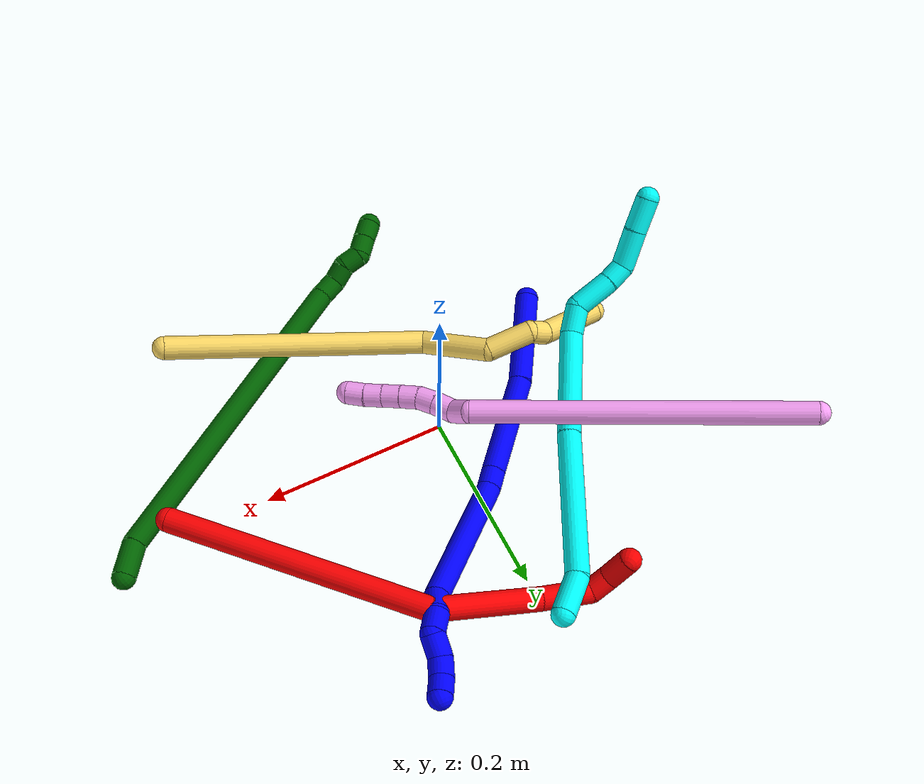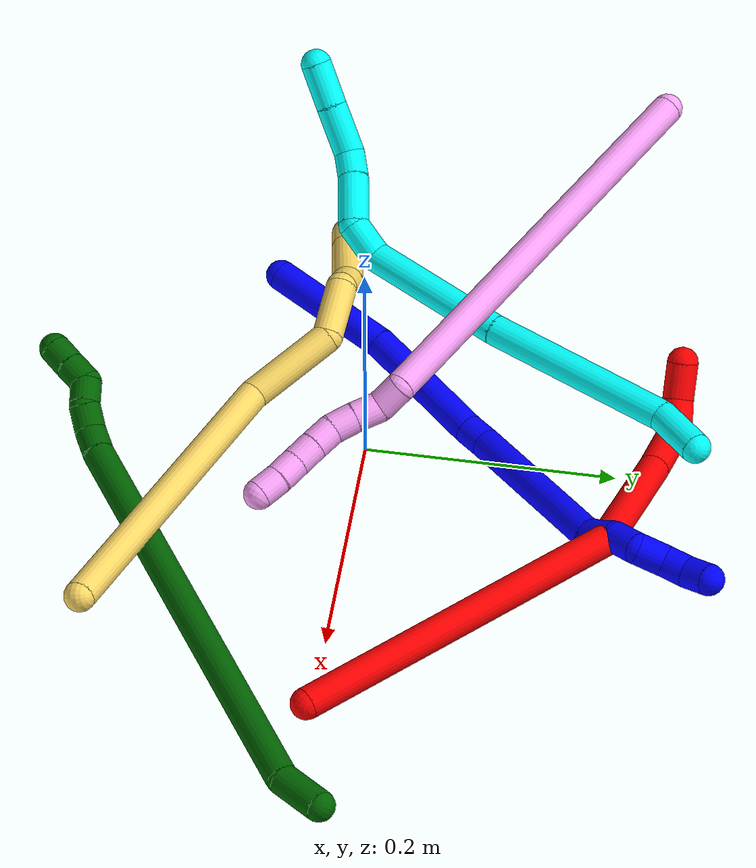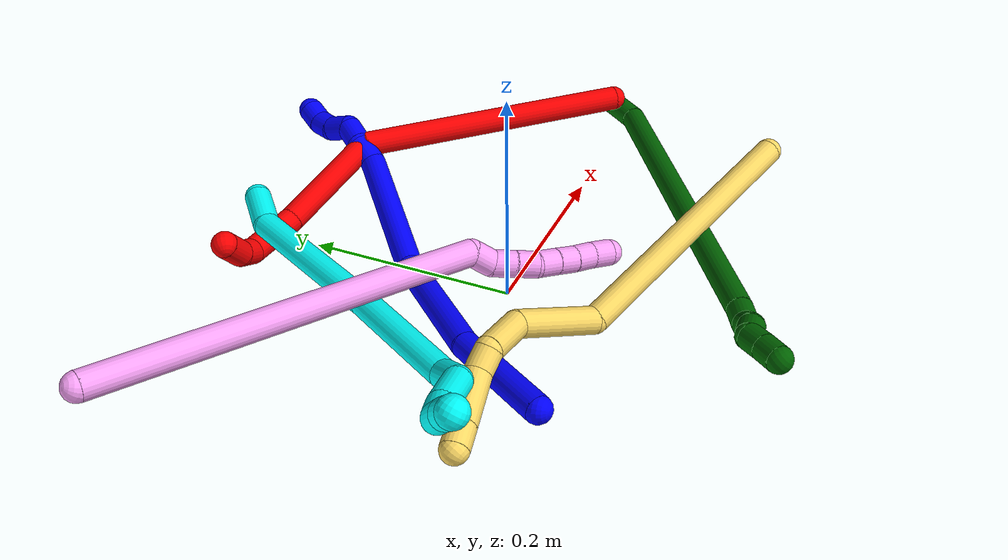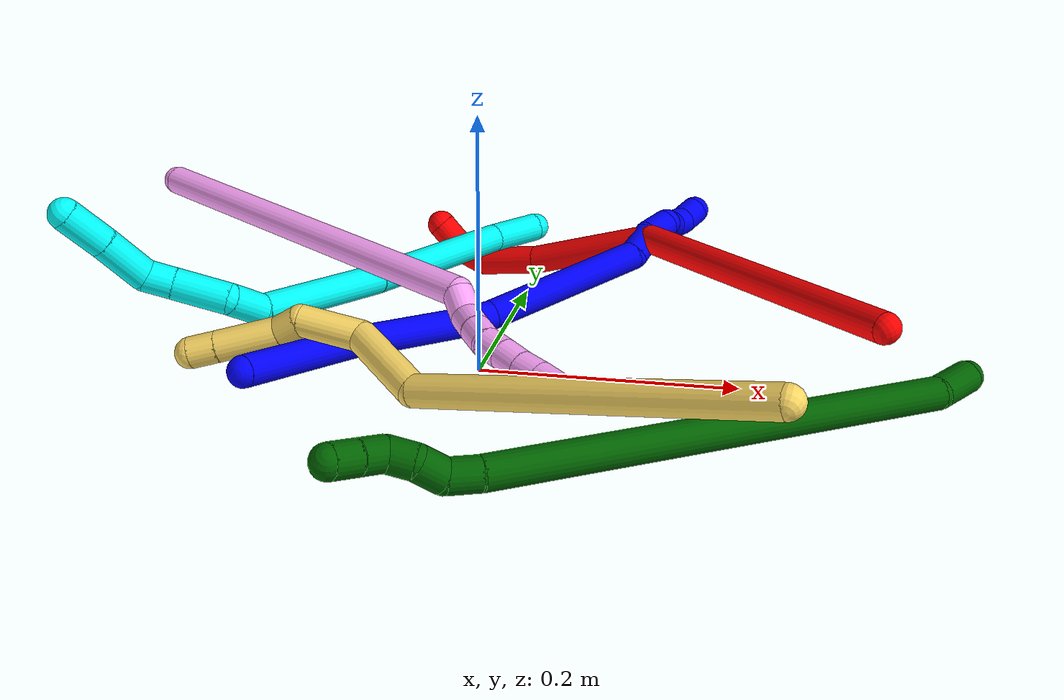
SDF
<sdf version="1.7">
 <world name="default">
  <plugin name="TubeGeneratorPlugin" filename="libtube_generator_plugin.so"/>
  <model name="photoneo_s_sensor">
   <static>1</static>
   <pose>0 0 2 1.57079 1.57079 3.14159</pose>
   <link name="link">
    <inertial><mass>0.1</mass></inertial>
    <sensor name="sensor" type="depth">
     <update_rate>30</update_rate>
     <camera>
      <horizontal_fov>1.22</horizontal_fov>
      <image><width>1920</width><height>1200</height><format>B8G8R8</format></image>
      <clip><near>0.1</near><far>4</far></clip>
      <depth_camera><output>points</output></depth_camera>
     </camera>
     <plugin name="camera_plugin" filename="libgazebo_ros_depth_camera.so">
      <baseline>0.2</baseline>
      <alwaysOn>1</alwaysOn>
      <updateRate>0.0</updateRate>
      <cameraName>camera_ir</cameraName>
      <imageTopicName>/camera/color/image_raw</imageTopicName>
      <cameraInfoTopicName>/camera/color/camera_info</cameraInfoTopicName>
      <depthImageTopicName>/camera/depth/image_raw</depthImageTopicName>
      <depthImageCameraInfoTopicName>/camera/depth/camera_info</depthImageCameraInfoTopicName>
      <pointCloudTopicName>/camera/depth/points</pointCloudTopicName>
      <frameName>fr_optical</frameName>
      <pointCloudCutoff>0.1</pointCloudCutoff>
      <pointCloudCutoffMax>2.0</pointCloudCutoffMax>
      <distortionK1>0</distortionK1>
      <distortionK2>0</distortionK2>
      <distortionK3>0</distortionK3>
      <distortionT1>0</distortionT1>
      <distortionT2>0</distortionT2>
      <CxPrime>0</CxPrime>
      <Cx>0</Cx>
      <Cy>0</Cy>
      <focalLength>0</focalLength>
      <hackBaseline>0</hackBaseline>
     </plugin>
    </sensor>
   </link>
  </model>
  <gravity>0 0 -9.8</gravity>
  <magnetic_field>6e-06 2.3e-05 -4.2e-05</magnetic_field>
  <atmosphere type="adiabatic"/>
  <physics name="default_physics" default="0" type="ode">
   <max_step_size>0.003</max_step_size>
   <real_time_factor>1</real_time_factor>
   <real_time_update_rate>1000</real_time_update_rate>
   <max_contacts>10000</max_contacts>
   <ode>
    <solver>
     <type>quick</type>
     <iters>100</iters>
     <sor>1.3</sor>
     <use_dynamic_moi_rescaling>0</use_dynamic_moi_rescaling>
    </solver>
    <constraints>
     <contact_max_correcting_vel>0</contact_max_correcting_vel>
     <contact_surface_layer>0.001</contact_surface_layer>
     <cfm>0</cfm>
     <erp>0.2</erp>
    </constraints>
   </ode>
  </physics>
  <scene><ambient>0.4 0.4 0.4 1</ambient><background>0.7 0.7 0.7 1</background><shadows>0</shadows></scene>
  <audio><device>default</device></audio>
  <spherical_coordinates>
   <surface_model>EARTH_WGS84</surface_model>
   <latitude_deg>0</latitude_deg>
   <longitude_deg>0</longitude_deg>
   <elevation>0</elevation>
   <heading_deg>0</heading_deg>
  </spherical_coordinates>
  <model name="bin">
   <static>1</static>
   <link name="bottom">
    <collision name="collision-bottom">
     <pose>0 0 -0.01 0 -0 0</pose>
     <geometry><box><size>0.8 0.6 0.02</size></box></geometry>
     <surface>
      <friction><ode><mu>100</mu><mu2>100</mu2></ode></friction>
      <contact><collide_bitmask>65535</collide_bitmask></contact>
     </surface>
    </collision>
   </link>
   <link name="west_wall">
    <collision name="collision-west_wall">
     <pose>-0.41 0 0.1 0 -0 0</pose>
     <geometry><box><size>0.02 0.6 0.2</size></box></geometry>
     <surface>
      <friction><ode><mu>100</mu><mu2>100</mu2></ode></friction>
      <contact><collide_bitmask>65535</collide_bitmask></contact>
     </surface>
    </collision>
   </link>
   <link name="east_wall">
    <collision name="collision-east_wall">
     <pose>0.41 0 0.1 0 -0 0</pose>
     <geometry><box><size>0.02 0.6 0.2</size></box></geometry>
     <surface>
      <friction><ode><mu>100</mu><mu2>100</mu2></ode></friction>
      <contact><collide_bitmask>65535</collide_bitmask></contact>
     </surface>
    </collision>
   </link>
   <link name="south_wall">
    <collision name="collision-south_wall">
     <pose>0 -0.31 0.1 0 -0 0</pose>
     <geometry><box><size>0.8 0.02 0.2</size></box></geometry>
     <surface>
      <friction><ode><mu>100</mu><mu2>100</mu2></ode></friction>
      <contact><collide_bitmask>65535</collide_bitmask></contact>
     </surface>
    </collision>
   </link>
   <link name="north_wall">
    <collision name="collision-north_wall">
     <pose>0 0.31 0.1 0 -0 0</pose>
     <geometry><box><size>0.8 0.02 0.2</size></box></geometry>
     <surface>
      <friction><ode><mu>100</mu><mu2>100</mu2></ode></friction>
      <contact><collide_bitmask>65535</collide_bitmask></contact>
     </surface>
    </collision>
   </link>
  </model>
  <model name="1">
   <static>0</static>
   <link name="1">
    <collision name="collision-cylinder-e_1_1_4">
     <pose>0.026451 0.00169 0.045942 -0.036772 0.522102 -0.009825</pose>
     <geometry><cylinder><radius>0.0125</radius><length>0.106079</length></cylinder></geometry>
     <surface>
      <friction><ode><mu>1.16</mu><mu2>1.16</mu2><slip1>0</slip1><slip2>0</slip2></ode></friction>
      <contact><ode><kp>1e+06</kp><kd>1</kd><max_vel>0</max_vel><min_depth>0.001</min_depth></ode></contact>
     </surface>
    </collision>
    <visual name="visual-cylinder-e_1_1_4">
     <pose>0.026451 0.00169 0.045942 -0.036772 0.522102 -0.009825</pose>
     <geometry><cylinder><radius>0.0125</radius><length>0.106079</length></cylinder></geometry>
     <material><ambient>0 0 1 1</ambient></material>
    </visual>
    <collision name="collision-cylinder-e_2_4_5">
     <pose>0.088689 0.007855 0.134403 -0.104845 0.696934 -0.03812</pose>
     <geometry><cylinder><radius>0.0125</radius><length>0.111509</length></cylinder></geometry>
     <surface>
      <friction><ode><mu>1.16</mu><mu2>1.16</mu2><slip1>0</slip1><slip2>0</slip2></ode></friction>
      <contact><ode><kp>1e+06</kp><kd>1</kd><max_vel>0</max_vel><min_depth>0.001</min_depth></ode></contact>
     </surface>
    </collision>
    <visual name="visual-cylinder-e_2_4_5">
     <pose>0.088689 0.007855 0.134403 -0.104845 0.696934 -0.03812</pose>
     <geometry><cylinder><radius>0.0125</radius><length>0.111509</length></cylinder></geometry>
     <material><ambient>0 0 1 1</ambient></material>
    </visual>
    <collision name="collision-cylinder-e_3_5_6">
     <pose>0.131276 0.012189 0.185047 0.017265 0.696705 0.00627</pose>
     <geometry><cylinder><radius>0.0125</radius><length>0.021194</length></cylinder></geometry>
     <surface>
      <friction><ode><mu>1.16</mu><mu2>1.16</mu2><slip1>0</slip1><slip2>0</slip2></ode></friction>
      <contact><ode><kp>1e+06</kp><kd>1</kd><max_vel>0</max_vel><min_depth>0.001</min_depth></ode></contact>
     </surface>
    </collision>
    <visual name="visual-cylinder-e_3_5_6">
     <pose>0.131276 0.012189 0.185047 0.017265 0.696705 0.00627</pose>
     <geometry><cylinder><radius>0.0125</radius><length>0.021194</length></cylinder></geometry>
     <material><ambient>0 0 1 1</ambient></material>
    </visual>
    <collision name="collision-cylinder-e_4_6_7">
     <pose>0.19371 0.00181 0.239351 0.218181 0.866195 0.101197</pose>
     <geometry><cylinder><radius>0.0125</radius><length>0.146047</length></cylinder></geometry>
     <surface>
      <friction><ode><mu>1.16</mu><mu2>1.16</mu2><slip1>0</slip1><slip2>0</slip2></ode></friction>
      <contact><ode><kp>1e+06</kp><kd>1</kd><max_vel>0</max_vel><min_depth>0.001</min_depth></ode></contact>
     </surface>
    </collision>
    <visual name="visual-cylinder-e_4_6_7">
     <pose>0.19371 0.00181 0.239351 0.218181 0.866195 0.101197</pose>
     <geometry><cylinder><radius>0.0125</radius><length>0.146047</length></cylinder></geometry>
     <material><ambient>0 0 1 1</ambient></material>
    </visual>
    <collision name="collision-cylinder-e_5_7_8">
     <pose>0.25574 -0.015347 0.294966 0.632609 0.500225 0.166834</pose>
     <geometry><cylinder><radius>0.0125</radius><length>0.02667</length></cylinder></geometry>
     <surface>
      <friction><ode><mu>1.16</mu><mu2>1.16</mu2><slip1>0</slip1><slip2>0</slip2></ode></friction>
      <contact><ode><kp>1e+06</kp><kd>1</kd><max_vel>0</max_vel><min_depth>0.001</min_depth></ode></contact>
     </surface>
    </collision>
    <visual name="visual-cylinder-e_5_7_8">
     <pose>0.25574 -0.015347 0.294966 0.632609 0.500225 0.166834</pose>
     <geometry><cylinder><radius>0.0125</radius><length>0.02667</length></cylinder></geometry>
     <material><ambient>0 0 1 1</ambient></material>
    </visual>
    <collision name="collision-cylinder-e_6_8_9">
     <pose>0.26962 -0.02511 0.313443 0.304909 0.668431 0.106604</pose>
     <geometry><cylinder><radius>0.0125</radius><length>0.024151</length></cylinder></geometry>
     <surface>
      <friction><ode><mu>1.16</mu><mu2>1.16</mu2><slip1>0</slip1><slip2>0</slip2></ode></friction>
      <contact><ode><kp>1e+06</kp><kd>1</kd><max_vel>0</max_vel><min_depth>0.001</min_depth></ode></contact>
     </surface>
    </collision>
    <visual name="visual-cylinder-e_6_8_9">
     <pose>0.26962 -0.02511 0.313443 0.304909 0.668431 0.106604</pose>
     <geometry><cylinder><radius>0.0125</radius><length>0.024151</length></cylinder></geometry>
     <material><ambient>0 0 1 1</ambient></material>
    </visual>
    <collision name="collision-cylinder-e_7_9_10">
     <pose>0.27748 -0.025844 0.334129 -0.179329 0.03179 -0.002858</pose>
     <geometry><cylinder><radius>0.0125</radius><length>0.023684</length></cylinder></geometry>
     <surface>
      <friction><ode><mu>1.16</mu><mu2>1.16</mu2><slip1>0</slip1><slip2>0</slip2></ode></friction>
      <contact><ode><kp>1e+06</kp><kd>1</kd><max_vel>0</max_vel><min_depth>0.001</min_depth></ode></contact>
     </surface>
    </collision>
    <visual name="visual-cylinder-e_7_9_10">
     <pose>0.27748 -0.025844 0.334129 -0.179329 0.03179 -0.002858</pose>
     <geometry><cylinder><radius>0.0125</radius><length>0.023684</length></cylinder></geometry>
     <material><ambient>0 0 1 1</ambient></material>
    </visual>
    <collision name="collision-cylinder-e_8_10_11">
     <pose>0.281664 -0.024154 0.355162 0.044833 0.385001 0.00874</pose>
     <geometry><cylinder><radius>0.0125</radius><length>0.020277</length></cylinder></geometry>
     <surface>
      <friction><ode><mu>1.16</mu><mu2>1.16</mu2><slip1>0</slip1><slip2>0</slip2></ode></friction>
      <contact><ode><kp>1e+06</kp><kd>1</kd><max_vel>0</max_vel><min_depth>0.001</min_depth></ode></contact>
     </surface>
    </collision>
    <visual name="visual-cylinder-e_8_10_11">
     <pose>0.281664 -0.024154 0.355162 0.044833 0.385001 0.00874</pose>
     <geometry><cylinder><radius>0.0125</radius><length>0.020277</length></cylinder></geometry>
     <material><ambient>0 0 1 1</ambient></material>
    </visual>
    <collision name="collision-cylinder-e_9_11_2">
     <pose>0.290997 -0.027704 0.372524 0.373934 0.572766 0.111302</pose>
     <geometry><cylinder><radius>0.0125</radius><length>0.02039</length></cylinder></geometry>
     <surface>
      <friction><ode><mu>1.16</mu><mu2>1.16</mu2><slip1>0</slip1><slip2>0</slip2></ode></friction>
      <contact><ode><kp>1e+06</kp><kd>1</kd><max_vel>0</max_vel><min_depth>0.001</min_depth></ode></contact>
     </surface>
    </collision>
    <visual name="visual-cylinder-e_9_11_2">
     <pose>0.290997 -0.027704 0.372524 0.373934 0.572766 0.111302</pose>
     <geometry><cylinder><radius>0.0125</radius><length>0.02039</length></cylinder></geometry>
     <material><ambient>0 0 1 1</ambient></material>
    </visual>
    <collision name="collision-sphere-2">
     <pose>0.296522 -0.030834 0.3805 0 -0 0</pose>
     <geometry><sphere><radius>0.0125</radius></sphere></geometry>
     <surface>
      <friction><ode><mu>1.16</mu><mu2>1.16</mu2><slip1>0</slip1><slip2>0</slip2></ode></friction>
      <contact><ode><kp>1e+06</kp><kd>1</kd><max_vel>0</max_vel><min_depth>0.001</min_depth></ode></contact>
     </surface>
    </collision>
    <visual name="visual-sphere-2">
     <pose>0.296522 -0.030834 0.3805 0 -0 0</pose>
     <geometry><sphere><radius>0.0125</radius></sphere></geometry>
     <material><ambient>0 0 1 1</ambient></material>
    </visual>
    <collision name="collision-sphere-11">
     <pose>0.285472 -0.024575 0.364549 0 -0 0</pose>
     <geometry><sphere><radius>0.0125</radius></sphere></geometry>
     <surface>
      <friction><ode><mu>1.16</mu><mu2>1.16</mu2><slip1>0</slip1><slip2>0</slip2></ode></friction>
      <contact><ode><kp>1e+06</kp><kd>1</kd><max_vel>0</max_vel><min_depth>0.001</min_depth></ode></contact>
     </surface>
    </collision>
    <visual name="visual-sphere-11">
     <pose>0.285472 -0.024575 0.364549 0 -0 0</pose>
     <geometry><sphere><radius>0.0125</radius></sphere></geometry>
     <material><ambient>0 0 1 1</ambient></material>
    </visual>
    <collision name="collision-sphere-10">
     <pose>0.277857 -0.023732 0.345775 0 -0 0</pose>
     <geometry><sphere><radius>0.0125</radius></sphere></geometry>
     <surface>
      <friction><ode><mu>1.16</mu><mu2>1.16</mu2><slip1>0</slip1><slip2>0</slip2></ode></friction>
      <contact><ode><kp>1e+06</kp><kd>1</kd><max_vel>0</max_vel><min_depth>0.001</min_depth></ode></contact>
     </surface>
    </collision>
    <visual name="visual-sphere-10">
     <pose>0.277857 -0.023732 0.345775 0 -0 0</pose>
     <geometry><sphere><radius>0.0125</radius></sphere></geometry>
     <material><ambient>0 0 1 1</ambient></material>
    </visual>
    <collision name="collision-sphere-9">
     <pose>0.277104 -0.027955 0.322482 0 -0 0</pose>
     <geometry><sphere><radius>0.0125</radius></sphere></geometry>
     <surface>
      <friction><ode><mu>1.16</mu><mu2>1.16</mu2><slip1>0</slip1><slip2>0</slip2></ode></friction>
      <contact><ode><kp>1e+06</kp><kd>1</kd><max_vel>0</max_vel><min_depth>0.001</min_depth></ode></contact>
     </surface>
    </collision>
    <visual name="visual-sphere-9">
     <pose>0.277104 -0.027955 0.322482 0 -0 0</pose>
     <geometry><sphere><radius>0.0125</radius></sphere></geometry>
     <material><ambient>0 0 1 1</ambient></material>
    </visual>
    <collision name="collision-sphere-4">
     <pose>0.052902 0.00338 0.091884 0 -0 0</pose>
     <geometry><sphere><radius>0.0125</radius></sphere></geometry>
     <surface>
      <friction><ode><mu>1.16</mu><mu2>1.16</mu2><slip1>0</slip1><slip2>0</slip2></ode></friction>
      <contact><ode><kp>1e+06</kp><kd>1</kd><max_vel>0</max_vel><min_depth>0.001</min_depth></ode></contact>
     </surface>
    </collision>
    <visual name="visual-sphere-4">
     <pose>0.052902 0.00338 0.091884 0 -0 0</pose>
     <geometry><sphere><radius>0.0125</radius></sphere></geometry>
     <material><ambient>0 0 1 1</ambient></material>
    </visual>
    <collision name="collision-sphere-1">
     <geometry><sphere><radius>0.0125</radius></sphere></geometry>
     <surface>
      <friction><ode><mu>1.16</mu><mu2>1.16</mu2><slip1>0</slip1><slip2>0</slip2></ode></friction>
      <contact><ode><kp>1e+06</kp><kd>1</kd><max_vel>0</max_vel><min_depth>0.001</min_depth></ode></contact>
     </surface>
    </collision>
    <visual name="visual-sphere-1">
     <geometry><sphere><radius>0.0125</radius></sphere></geometry>
     <material><ambient>0 0 1 1</ambient></material>
    </visual>
    <collision name="collision-sphere-8">
     <pose>0.262136 -0.022265 0.304403 0 -0 0</pose>
     <geometry><sphere><radius>0.0125</radius></sphere></geometry>
     <surface>
      <friction><ode><mu>1.16</mu><mu2>1.16</mu2><slip1>0</slip1><slip2>0</slip2></ode></friction>
      <contact><ode><kp>1e+06</kp><kd>1</kd><max_vel>0</max_vel><min_depth>0.001</min_depth></ode></contact>
     </surface>
    </collision>
    <visual name="visual-sphere-8">
     <pose>0.262136 -0.022265 0.304403 0 -0 0</pose>
     <geometry><sphere><radius>0.0125</radius></sphere></geometry>
     <material><ambient>0 0 1 1</ambient></material>
    </visual>
    <collision name="collision-sphere-5">
     <pose>0.124476 0.012329 0.176921 0 -0 0</pose>
     <geometry><sphere><radius>0.0125</radius></sphere></geometry>
     <surface>
      <friction><ode><mu>1.16</mu><mu2>1.16</mu2><slip1>0</slip1><slip2>0</slip2></ode></friction>
      <contact><ode><kp>1e+06</kp><kd>1</kd><max_vel>0</max_vel><min_depth>0.001</min_depth></ode></contact>
     </surface>
    </collision>
    <visual name="visual-sphere-5">
     <pose>0.124476 0.012329 0.176921 0 -0 0</pose>
     <geometry><sphere><radius>0.0125</radius></sphere></geometry>
     <material><ambient>0 0 1 1</ambient></material>
    </visual>
    <collision name="collision-sphere-6">
     <pose>0.138076 0.012048 0.193173 0 -0 0</pose>
     <geometry><sphere><radius>0.0125</radius></sphere></geometry>
     <surface>
      <friction><ode><mu>1.16</mu><mu2>1.16</mu2><slip1>0</slip1><slip2>0</slip2></ode></friction>
      <contact><ode><kp>1e+06</kp><kd>1</kd><max_vel>0</max_vel><min_depth>0.001</min_depth></ode></contact>
     </surface>
    </collision>
    <visual name="visual-sphere-6">
     <pose>0.138076 0.012048 0.193173 0 -0 0</pose>
     <geometry><sphere><radius>0.0125</radius></sphere></geometry>
     <material><ambient>0 0 1 1</ambient></material>
    </visual>
    <collision name="collision-sphere-7">
     <pose>0.249345 -0.008428 0.28553 0 -0 0</pose>
     <geometry><sphere><radius>0.0125</radius></sphere></geometry>
     <surface>
      <friction><ode><mu>1.16</mu><mu2>1.16</mu2><slip1>0</slip1><slip2>0</slip2></ode></friction>
      <contact><ode><kp>1e+06</kp><kd>1</kd><max_vel>0</max_vel><min_depth>0.001</min_depth></ode></contact>
     </surface>
    </collision>
    <visual name="visual-sphere-7">
     <pose>0.249345 -0.008428 0.28553 0 -0 0</pose>
     <geometry><sphere><radius>0.0125</radius></sphere></geometry>
     <material><ambient>0 0 1 1</ambient></material>
    </visual>
    <inertial>
     <pose>0.150634 -0.002209 0.193773 0 -0 0</pose>
     <mass>0.5</mass>
     <inertia>
      <ixx>0.000399</ixx>
      <ixy>0</ixy>
      <ixz>0</ixz>
      <iyy>0.000507</iyy>
      <iyz>0</iyz>
      <izz>-0.00028</izz>
     </inertia>
    </inertial>
   </link>
   <pose>-0.15592 -0.092808 0.022621 -1.74026 -0.239606 -0.003966</pose>
  </model>
  <model name="2">
   <static>0</static>
   <link name="2">
    <collision name="collision-cylinder-e_1_1_4">
     <pose>-0.134992 0.032664 0.010885 -1.24913 -1.32107 1.02106</pose>
     <geometry><cylinder><radius>0.0125</radius><length>0.278628</length></cylinder></geometry>
     <surface>
      <friction><ode><mu>1.16</mu><mu2>1.16</mu2><slip1>0</slip1><slip2>0</slip2></ode></friction>
      <contact><ode><kp>1e+06</kp><kd>1</kd><max_vel>0</max_vel><min_depth>0.001</min_depth></ode></contact>
     </surface>
    </collision>
    <visual name="visual-cylinder-e_1_1_4">
     <pose>-0.134992 0.032664 0.010885 -1.24913 -1.32107 1.02106</pose>
     <geometry><cylinder><radius>0.0125</radius><length>0.278628</length></cylinder></geometry>
     <material><ambient>1 0 0 1</ambient></material>
    </visual>
    <collision name="collision-cylinder-e_2_4_5">
     <pose>-0.313024 0.071736 0.058801 -0.171372 -0.853 0.078022</pose>
     <geometry><cylinder><radius>0.0125</radius><length>0.114276</length></cylinder></geometry>
     <surface>
      <friction><ode><mu>1.16</mu><mu2>1.16</mu2><slip1>0</slip1><slip2>0</slip2></ode></friction>
      <contact><ode><kp>1e+06</kp><kd>1</kd><max_vel>0</max_vel><min_depth>0.001</min_depth></ode></contact>
     </surface>
    </collision>
    <visual name="visual-cylinder-e_2_4_5">
     <pose>-0.313024 0.071736 0.058801 -0.171372 -0.853 0.078022</pose>
     <geometry><cylinder><radius>0.0125</radius><length>0.114276</length></cylinder></geometry>
     <material><ambient>1 0 0 1</ambient></material>
    </visual>
    <collision name="collision-cylinder-e_3_5_6">
     <pose>-0.376294 0.085012 0.112254 -0.396032 -0.849187 0.180926</pose>
     <geometry><cylinder><radius>0.0125</radius><length>0.053892</length></cylinder></geometry>
     <surface>
      <friction><ode><mu>1.16</mu><mu2>1.16</mu2><slip1>0</slip1><slip2>0</slip2></ode></friction>
      <contact><ode><kp>1e+06</kp><kd>1</kd><max_vel>0</max_vel><min_depth>0.001</min_depth></ode></contact>
     </surface>
    </collision>
    <visual name="visual-cylinder-e_3_5_6">
     <pose>-0.376294 0.085012 0.112254 -0.396032 -0.849187 0.180926</pose>
     <geometry><cylinder><radius>0.0125</radius><length>0.053892</length></cylinder></geometry>
     <material><ambient>1 0 0 1</ambient></material>
    </visual>
    <collision name="collision-cylinder-e_4_6_7">
     <pose>-0.400435 0.101116 0.134274 -1.02604 -0.34748 0.197098</pose>
     <geometry><cylinder><radius>0.0125</radius><length>0.022973</length></cylinder></geometry>
     <surface>
      <friction><ode><mu>1.16</mu><mu2>1.16</mu2><slip1>0</slip1><slip2>0</slip2></ode></friction>
      <contact><ode><kp>1e+06</kp><kd>1</kd><max_vel>0</max_vel><min_depth>0.001</min_depth></ode></contact>
     </surface>
    </collision>
    <visual name="visual-cylinder-e_4_6_7">
     <pose>-0.400435 0.101116 0.134274 -1.02604 -0.34748 0.197098</pose>
     <geometry><cylinder><radius>0.0125</radius><length>0.022973</length></cylinder></geometry>
     <material><ambient>1 0 0 1</ambient></material>
    </visual>
    <collision name="collision-cylinder-e_5_7_2">
     <pose>-0.407946 0.124791 0.142521 -1.38922 -0.240432 0.200603</pose>
     <geometry><cylinder><radius>0.0125</radius><length>0.03023</length></cylinder></geometry>
     <surface>
      <friction><ode><mu>1.16</mu><mu2>1.16</mu2><slip1>0</slip1><slip2>0</slip2></ode></friction>
      <contact><ode><kp>1e+06</kp><kd>1</kd><max_vel>0</max_vel><min_depth>0.001</min_depth></ode></contact>
     </surface>
    </collision>
    <visual name="visual-cylinder-e_5_7_2">
     <pose>-0.407946 0.124791 0.142521 -1.38922 -0.240432 0.200603</pose>
     <geometry><cylinder><radius>0.0125</radius><length>0.03023</length></cylinder></geometry>
     <material><ambient>1 0 0 1</ambient></material>
    </visual>
    <collision name="collision-sphere-2">
     <pose>-0.411545 0.139231 0.145172 0 -0 0</pose>
     <geometry><sphere><radius>0.0125</radius></sphere></geometry>
     <surface>
      <friction><ode><mu>1.16</mu><mu2>1.16</mu2><slip1>0</slip1><slip2>0</slip2></ode></friction>
      <contact><ode><kp>1e+06</kp><kd>1</kd><max_vel>0</max_vel><min_depth>0.001</min_depth></ode></contact>
     </surface>
    </collision>
    <visual name="visual-sphere-2">
     <pose>-0.411545 0.139231 0.145172 0 -0 0</pose>
     <geometry><sphere><radius>0.0125</radius></sphere></geometry>
     <material><ambient>1 0 0 1</ambient></material>
    </visual>
    <collision name="collision-sphere-7">
     <pose>-0.404347 0.110352 0.13987 0 -0 0</pose>
     <geometry><sphere><radius>0.0125</radius></sphere></geometry>
     <surface>
      <friction><ode><mu>1.16</mu><mu2>1.16</mu2><slip1>0</slip1><slip2>0</slip2></ode></friction>
      <contact><ode><kp>1e+06</kp><kd>1</kd><max_vel>0</max_vel><min_depth>0.001</min_depth></ode></contact>
     </surface>
    </collision>
    <visual name="visual-sphere-7">
     <pose>-0.404347 0.110352 0.13987 0 -0 0</pose>
     <geometry><sphere><radius>0.0125</radius></sphere></geometry>
     <material><ambient>1 0 0 1</ambient></material>
    </visual>
    <collision name="collision-sphere-6">
     <pose>-0.396523 0.091879 0.128677 0 -0 0</pose>
     <geometry><sphere><radius>0.0125</radius></sphere></geometry>
     <surface>
      <friction><ode><mu>1.16</mu><mu2>1.16</mu2><slip1>0</slip1><slip2>0</slip2></ode></friction>
      <contact><ode><kp>1e+06</kp><kd>1</kd><max_vel>0</max_vel><min_depth>0.001</min_depth></ode></contact>
     </surface>
    </collision>
    <visual name="visual-sphere-6">
     <pose>-0.396523 0.091879 0.128677 0 -0 0</pose>
     <geometry><sphere><radius>0.0125</radius></sphere></geometry>
     <material><ambient>1 0 0 1</ambient></material>
    </visual>
    <collision name="collision-sphere-5">
     <pose>-0.356064 0.078145 0.095831 0 -0 0</pose>
     <geometry><sphere><radius>0.0125</radius></sphere></geometry>
     <surface>
      <friction><ode><mu>1.16</mu><mu2>1.16</mu2><slip1>0</slip1><slip2>0</slip2></ode></friction>
      <contact><ode><kp>1e+06</kp><kd>1</kd><max_vel>0</max_vel><min_depth>0.001</min_depth></ode></contact>
     </surface>
    </collision>
    <visual name="visual-sphere-5">
     <pose>-0.356064 0.078145 0.095831 0 -0 0</pose>
     <geometry><sphere><radius>0.0125</radius></sphere></geometry>
     <material><ambient>1 0 0 1</ambient></material>
    </visual>
    <collision name="collision-sphere-1">
     <geometry><sphere><radius>0.0125</radius></sphere></geometry>
     <surface>
      <friction><ode><mu>1.16</mu><mu2>1.16</mu2><slip1>0</slip1><slip2>0</slip2></ode></friction>
      <contact><ode><kp>1e+06</kp><kd>1</kd><max_vel>0</max_vel><min_depth>0.001</min_depth></ode></contact>
     </surface>
    </collision>
    <visual name="visual-sphere-1">
     <geometry><sphere><radius>0.0125</radius></sphere></geometry>
     <material><ambient>1 0 0 1</ambient></material>
    </visual>
    <collision name="collision-sphere-4">
     <pose>-0.269985 0.065327 0.02177 0 -0 0</pose>
     <geometry><sphere><radius>0.0125</radius></sphere></geometry>
     <surface>
      <friction><ode><mu>1.16</mu><mu2>1.16</mu2><slip1>0</slip1><slip2>0</slip2></ode></friction>
      <contact><ode><kp>1e+06</kp><kd>1</kd><max_vel>0</max_vel><min_depth>0.001</min_depth></ode></contact>
     </surface>
    </collision>
    <visual name="visual-sphere-4">
     <pose>-0.269985 0.065327 0.02177 0 -0 0</pose>
     <geometry><sphere><radius>0.0125</radius></sphere></geometry>
     <material><ambient>1 0 0 1</ambient></material>
    </visual>
    <inertial>
     <pose>-0.23039 0.055951 0.04639 0 -0 0</pose>
     <mass>0.5</mass>
     <inertia>
      <ixx>0.000693</ixx>
      <ixy>0</ixy>
      <ixz>0</ixz>
      <iyy>0.002268</iyy>
      <iyz>0</iyz>
      <izz>0.00143</izz>
     </inertia>
    </inertial>
   </link>
   <pose>0.301998 0.002478 0.054742 1.97298 -0.191042 -0.971519</pose>
  </model>
  <model name="3">
   <static>0</static>
   <link name="3">
    <collision name="collision-cylinder-e_1_1_4">
     <pose>-0.014583 -0.014326 0.009003 1.00972 -0.711336 -0.404942</pose>
     <geometry><cylinder><radius>0.0125</radius><length>0.044675</length></cylinder></geometry>
     <surface>
      <friction><ode><mu>1.16</mu><mu2>1.16</mu2><slip1>0</slip1><slip2>0</slip2></ode></friction>
      <contact><ode><kp>1e+06</kp><kd>1</kd><max_vel>0</max_vel><min_depth>0.001</min_depth></ode></contact>
     </surface>
    </collision>
    <visual name="visual-cylinder-e_1_1_4">
     <pose>-0.014583 -0.014326 0.009003 1.00972 -0.711336 -0.404942</pose>
     <geometry><cylinder><radius>0.0125</radius><length>0.044675</length></cylinder></geometry>
     <material><ambient>0.003922 1 0.996078 1</ambient></material>
    </visual>
    <collision name="collision-cylinder-e_2_4_5">
     <pose>-0.095884 -0.071334 0.024796 1.41305 -0.995989 -0.868953</pose>
     <geometry><cylinder><radius>0.0125</radius><length>0.158986</length></cylinder></geometry>
     <surface>
      <friction><ode><mu>1.16</mu><mu2>1.16</mu2><slip1>0</slip1><slip2>0</slip2></ode></friction>
      <contact><ode><kp>1e+06</kp><kd>1</kd><max_vel>0</max_vel><min_depth>0.001</min_depth></ode></contact>
     </surface>
    </collision>
    <visual name="visual-cylinder-e_2_4_5">
     <pose>-0.095884 -0.071334 0.024796 1.41305 -0.995989 -0.868953</pose>
     <geometry><cylinder><radius>0.0125</radius><length>0.158986</length></cylinder></geometry>
     <material><ambient>0.003922 1 0.996078 1</ambient></material>
    </visual>
    <collision name="collision-cylinder-e_3_5_6">
     <pose>-0.211192 -0.150126 0.038393 1.38444 -0.923298 -0.782419</pose>
     <geometry><cylinder><radius>0.0125</radius><length>0.121841</length></cylinder></geometry>
     <surface>
      <friction><ode><mu>1.16</mu><mu2>1.16</mu2><slip1>0</slip1><slip2>0</slip2></ode></friction>
      <contact><ode><kp>1e+06</kp><kd>1</kd><max_vel>0</max_vel><min_depth>0.001</min_depth></ode></contact>
     </surface>
    </collision>
    <visual name="visual-cylinder-e_3_5_6">
     <pose>-0.211192 -0.150126 0.038393 1.38444 -0.923298 -0.782419</pose>
     <geometry><cylinder><radius>0.0125</radius><length>0.121841</length></cylinder></geometry>
     <material><ambient>0.003922 1 0.996078 1</ambient></material>
    </visual>
    <collision name="collision-cylinder-e_4_6_7">
     <pose>-0.267177 -0.199875 0.043553 1.69113 -0.493818 -0.554105</pose>
     <geometry><cylinder><radius>0.0125</radius><length>0.031202</length></cylinder></geometry>
     <surface>
      <friction><ode><mu>1.16</mu><mu2>1.16</mu2><slip1>0</slip1><slip2>0</slip2></ode></friction>
      <contact><ode><kp>1e+06</kp><kd>1</kd><max_vel>0</max_vel><min_depth>0.001</min_depth></ode></contact>
     </surface>
    </collision>
    <visual name="visual-cylinder-e_4_6_7">
     <pose>-0.267177 -0.199875 0.043553 1.69113 -0.493818 -0.554105</pose>
     <geometry><cylinder><radius>0.0125</radius><length>0.031202</length></cylinder></geometry>
     <material><ambient>0.003922 1 0.996078 1</ambient></material>
    </visual>
    <collision name="collision-cylinder-e_5_7_8">
     <pose>-0.275433 -0.233246 0.050791 1.14766 -0.039756 -0.025699</pose>
     <geometry><cylinder><radius>0.0125</radius><length>0.043319</length></cylinder></geometry>
     <surface>
      <friction><ode><mu>1.16</mu><mu2>1.16</mu2><slip1>0</slip1><slip2>0</slip2></ode></friction>
      <contact><ode><kp>1e+06</kp><kd>1</kd><max_vel>0</max_vel><min_depth>0.001</min_depth></ode></contact>
     </surface>
    </collision>
    <visual name="visual-cylinder-e_5_7_8">
     <pose>-0.275433 -0.233246 0.050791 1.14766 -0.039756 -0.025699</pose>
     <geometry><cylinder><radius>0.0125</radius><length>0.043319</length></cylinder></geometry>
     <material><ambient>0.003922 1 0.996078 1</ambient></material>
    </visual>
    <collision name="collision-cylinder-e_6_8_9">
     <pose>-0.278009 -0.263545 0.063202 1.2488 -0.152861 -0.110251</pose>
     <geometry><cylinder><radius>0.0125</radius><length>0.022538</length></cylinder></geometry>
     <surface>
      <friction><ode><mu>1.16</mu><mu2>1.16</mu2><slip1>0</slip1><slip2>0</slip2></ode></friction>
      <contact><ode><kp>1e+06</kp><kd>1</kd><max_vel>0</max_vel><min_depth>0.001</min_depth></ode></contact>
     </surface>
    </collision>
    <visual name="visual-cylinder-e_6_8_9">
     <pose>-0.278009 -0.263545 0.063202 1.2488 -0.152861 -0.110251</pose>
     <geometry><cylinder><radius>0.0125</radius><length>0.022538</length></cylinder></geometry>
     <material><ambient>0.003922 1 0.996078 1</ambient></material>
    </visual>
    <collision name="collision-cylinder-e_7_9_10">
     <pose>-0.283226 -0.293839 0.061635 1.82338 -0.170174 -0.219321</pose>
     <geometry><cylinder><radius>0.0125</radius><length>0.041348</length></cylinder></geometry>
     <surface>
      <friction><ode><mu>1.16</mu><mu2>1.16</mu2><slip1>0</slip1><slip2>0</slip2></ode></friction>
      <contact><ode><kp>1e+06</kp><kd>1</kd><max_vel>0</max_vel><min_depth>0.001</min_depth></ode></contact>
     </surface>
    </collision>
    <visual name="visual-cylinder-e_7_9_10">
     <pose>-0.283226 -0.293839 0.061635 1.82338 -0.170174 -0.219321</pose>
     <geometry><cylinder><radius>0.0125</radius><length>0.041348</length></cylinder></geometry>
     <material><ambient>0.003922 1 0.996078 1</ambient></material>
    </visual>
    <collision name="collision-cylinder-e_8_10_2">
     <pose>-0.289893 -0.330952 0.052881 1.77842 -0.176309 -0.217028</pose>
     <geometry><cylinder><radius>0.0125</radius><length>0.036091</length></cylinder></geometry>
     <surface>
      <friction><ode><mu>1.16</mu><mu2>1.16</mu2><slip1>0</slip1><slip2>0</slip2></ode></friction>
      <contact><ode><kp>1e+06</kp><kd>1</kd><max_vel>0</max_vel><min_depth>0.001</min_depth></ode></contact>
     </surface>
    </collision>
    <visual name="visual-cylinder-e_8_10_2">
     <pose>-0.289893 -0.330952 0.052881 1.77842 -0.176309 -0.217028</pose>
     <geometry><cylinder><radius>0.0125</radius><length>0.036091</length></cylinder></geometry>
     <material><ambient>0.003922 1 0.996078 1</ambient></material>
    </visual>
    <collision name="collision-sphere-2">
     <pose>-0.293058 -0.348336 0.049219 0 -0 0</pose>
     <geometry><sphere><radius>0.0125</radius></sphere></geometry>
     <surface>
      <friction><ode><mu>1.16</mu><mu2>1.16</mu2><slip1>0</slip1><slip2>0</slip2></ode></friction>
      <contact><ode><kp>1e+06</kp><kd>1</kd><max_vel>0</max_vel><min_depth>0.001</min_depth></ode></contact>
     </surface>
    </collision>
    <visual name="visual-sphere-2">
     <pose>-0.293058 -0.348336 0.049219 0 -0 0</pose>
     <geometry><sphere><radius>0.0125</radius></sphere></geometry>
     <material><ambient>0.003922 1 0.996078 1</ambient></material>
    </visual>
    <collision name="collision-sphere-10">
     <pose>-0.286728 -0.313568 0.056543 0 -0 0</pose>
     <geometry><sphere><radius>0.0125</radius></sphere></geometry>
     <surface>
      <friction><ode><mu>1.16</mu><mu2>1.16</mu2><slip1>0</slip1><slip2>0</slip2></ode></friction>
      <contact><ode><kp>1e+06</kp><kd>1</kd><max_vel>0</max_vel><min_depth>0.001</min_depth></ode></contact>
     </surface>
    </collision>
    <visual name="visual-sphere-10">
     <pose>-0.286728 -0.313568 0.056543 0 -0 0</pose>
     <geometry><sphere><radius>0.0125</radius></sphere></geometry>
     <material><ambient>0.003922 1 0.996078 1</ambient></material>
    </visual>
    <collision name="collision-sphere-9">
     <pose>-0.279725 -0.27411 0.066727 0 -0 0</pose>
     <geometry><sphere><radius>0.0125</radius></sphere></geometry>
     <surface>
      <friction><ode><mu>1.16</mu><mu2>1.16</mu2><slip1>0</slip1><slip2>0</slip2></ode></friction>
      <contact><ode><kp>1e+06</kp><kd>1</kd><max_vel>0</max_vel><min_depth>0.001</min_depth></ode></contact>
     </surface>
    </collision>
    <visual name="visual-sphere-9">
     <pose>-0.279725 -0.27411 0.066727 0 -0 0</pose>
     <geometry><sphere><radius>0.0125</radius></sphere></geometry>
     <material><ambient>0.003922 1 0.996078 1</ambient></material>
    </visual>
    <collision name="collision-sphere-4">
     <pose>-0.029166 -0.028652 0.018006 0 -0 0</pose>
     <geometry><sphere><radius>0.0125</radius></sphere></geometry>
     <surface>
      <friction><ode><mu>1.16</mu><mu2>1.16</mu2><slip1>0</slip1><slip2>0</slip2></ode></friction>
      <contact><ode><kp>1e+06</kp><kd>1</kd><max_vel>0</max_vel><min_depth>0.001</min_depth></ode></contact>
     </surface>
    </collision>
    <visual name="visual-sphere-4">
     <pose>-0.029166 -0.028652 0.018006 0 -0 0</pose>
     <geometry><sphere><radius>0.0125</radius></sphere></geometry>
     <material><ambient>0.003922 1 0.996078 1</ambient></material>
    </visual>
    <collision name="collision-sphere-1">
     <geometry><sphere><radius>0.0125</radius></sphere></geometry>
     <surface>
      <friction><ode><mu>1.16</mu><mu2>1.16</mu2><slip1>0</slip1><slip2>0</slip2></ode></friction>
      <contact><ode><kp>1e+06</kp><kd>1</kd><max_vel>0</max_vel><min_depth>0.001</min_depth></ode></contact>
     </surface>
    </collision>
    <visual name="visual-sphere-1">
     <geometry><sphere><radius>0.0125</radius></sphere></geometry>
     <material><ambient>0.003922 1 0.996078 1</ambient></material>
    </visual>
    <collision name="collision-sphere-8">
     <pose>-0.276293 -0.25298 0.059678 0 -0 0</pose>
     <geometry><sphere><radius>0.0125</radius></sphere></geometry>
     <surface>
      <friction><ode><mu>1.16</mu><mu2>1.16</mu2><slip1>0</slip1><slip2>0</slip2></ode></friction>
      <contact><ode><kp>1e+06</kp><kd>1</kd><max_vel>0</max_vel><min_depth>0.001</min_depth></ode></contact>
     </surface>
    </collision>
    <visual name="visual-sphere-8">
     <pose>-0.276293 -0.25298 0.059678 0 -0 0</pose>
     <geometry><sphere><radius>0.0125</radius></sphere></geometry>
     <material><ambient>0.003922 1 0.996078 1</ambient></material>
    </visual>
    <collision name="collision-sphere-5">
     <pose>-0.162602 -0.114015 0.031585 0 -0 0</pose>
     <geometry><sphere><radius>0.0125</radius></sphere></geometry>
     <surface>
      <friction><ode><mu>1.16</mu><mu2>1.16</mu2><slip1>0</slip1><slip2>0</slip2></ode></friction>
      <contact><ode><kp>1e+06</kp><kd>1</kd><max_vel>0</max_vel><min_depth>0.001</min_depth></ode></contact>
     </surface>
    </collision>
    <visual name="visual-sphere-5">
     <pose>-0.162602 -0.114015 0.031585 0 -0 0</pose>
     <geometry><sphere><radius>0.0125</radius></sphere></geometry>
     <material><ambient>0.003922 1 0.996078 1</ambient></material>
    </visual>
    <collision name="collision-sphere-6">
     <pose>-0.259782 -0.186237 0.045202 0 -0 0</pose>
     <geometry><sphere><radius>0.0125</radius></sphere></geometry>
     <surface>
      <friction><ode><mu>1.16</mu><mu2>1.16</mu2><slip1>0</slip1><slip2>0</slip2></ode></friction>
      <contact><ode><kp>1e+06</kp><kd>1</kd><max_vel>0</max_vel><min_depth>0.001</min_depth></ode></contact>
     </surface>
    </collision>
    <visual name="visual-sphere-6">
     <pose>-0.259782 -0.186237 0.045202 0 -0 0</pose>
     <geometry><sphere><radius>0.0125</radius></sphere></geometry>
     <material><ambient>0.003922 1 0.996078 1</ambient></material>
    </visual>
    <collision name="collision-sphere-7">
     <pose>-0.274572 -0.213513 0.041904 0 -0 0</pose>
     <geometry><sphere><radius>0.0125</radius></sphere></geometry>
     <surface>
      <friction><ode><mu>1.16</mu><mu2>1.16</mu2><slip1>0</slip1><slip2>0</slip2></ode></friction>
      <contact><ode><kp>1e+06</kp><kd>1</kd><max_vel>0</max_vel><min_depth>0.001</min_depth></ode></contact>
     </surface>
    </collision>
    <visual name="visual-sphere-7">
     <pose>-0.274572 -0.213513 0.041904 0 -0 0</pose>
     <geometry><sphere><radius>0.0125</radius></sphere></geometry>
     <material><ambient>0.003922 1 0.996078 1</ambient></material>
    </visual>
    <inertial>
     <pose>-0.180669 -0.153294 0.036926 0 -0 0</pose>
     <mass>0.5</mass>
     <inertia><ixx>-2e-05</ixx><ixy>0</ixy><ixz>0</ixz><iyy>0.000123</iyy><iyz>0</iyz><izz>0.000731</izz></inertia>
    </inertial>
   </link>
   <pose>-0.004179 0.260733 0.043158 -2.40845 -0.334215 1.58623</pose>
  </model>
  <model name="4">
   <static>0</static>
   <link name="4">
    <collision name="collision-cylinder-e_1_1_4">
     <pose>0.063911 -0.037507 -0.160657 2.91224 0.36959 2.03712</pose>
     <geometry><cylinder><radius>0.0125</radius><length>0.353848</length></cylinder></geometry>
     <surface>
      <friction><ode><mu>1.16</mu><mu2>1.16</mu2><slip1>0</slip1><slip2>0</slip2></ode></friction>
      <contact><ode><kp>1e+06</kp><kd>1</kd><max_vel>0</max_vel><min_depth>0.001</min_depth></ode></contact>
     </surface>
    </collision>
    <visual name="visual-cylinder-e_1_1_4">
     <pose>0.063911 -0.037507 -0.160657 2.91224 0.36959 2.03712</pose>
     <geometry><cylinder><radius>0.0125</radius><length>0.353848</length></cylinder></geometry>
     <material><ambient>1 0.65098 0.996078 1</ambient></material>
    </visual>
    <collision name="collision-cylinder-e_2_4_5">
     <pose>0.12395 -0.078086 -0.331938 2.86015 -0.336736 -1.75205</pose>
     <geometry><cylinder><radius>0.0125</radius><length>0.023435</length></cylinder></geometry>
     <surface>
      <friction><ode><mu>1.16</mu><mu2>1.16</mu2><slip1>0</slip1><slip2>0</slip2></ode></friction>
      <contact><ode><kp>1e+06</kp><kd>1</kd><max_vel>0</max_vel><min_depth>0.001</min_depth></ode></contact>
     </surface>
    </collision>
    <visual name="visual-cylinder-e_2_4_5">
     <pose>0.12395 -0.078086 -0.331938 2.86015 -0.336736 -1.75205</pose>
     <geometry><cylinder><radius>0.0125</radius><length>0.023435</length></cylinder></geometry>
     <material><ambient>1 0.65098 0.996078 1</ambient></material>
    </visual>
    <collision name="collision-cylinder-e_3_5_6">
     <pose>0.120835 -0.087766 -0.351557 2.50797 0.067684 0.205796</pose>
     <geometry><cylinder><radius>0.0125</radius><length>0.022374</length></cylinder></geometry>
     <surface>
      <friction><ode><mu>1.16</mu><mu2>1.16</mu2><slip1>0</slip1><slip2>0</slip2></ode></friction>
      <contact><ode><kp>1e+06</kp><kd>1</kd><max_vel>0</max_vel><min_depth>0.001</min_depth></ode></contact>
     </surface>
    </collision>
    <visual name="visual-cylinder-e_3_5_6">
     <pose>0.120835 -0.087766 -0.351557 2.50797 0.067684 0.205796</pose>
     <geometry><cylinder><radius>0.0125</radius><length>0.022374</length></cylinder></geometry>
     <material><ambient>1 0.65098 0.996078 1</ambient></material>
    </visual>
    <collision name="collision-cylinder-e_4_6_7">
     <pose>0.122295 -0.099672 -0.36911 2.58732 0.069722 0.243989</pose>
     <geometry><cylinder><radius>0.0125</radius><length>0.020179</length></cylinder></geometry>
     <surface>
      <friction><ode><mu>1.16</mu><mu2>1.16</mu2><slip1>0</slip1><slip2>0</slip2></ode></friction>
      <contact><ode><kp>1e+06</kp><kd>1</kd><max_vel>0</max_vel><min_depth>0.001</min_depth></ode></contact>
     </surface>
    </collision>
    <visual name="visual-cylinder-e_4_6_7">
     <pose>0.122295 -0.099672 -0.36911 2.58732 0.069722 0.243989</pose>
     <geometry><cylinder><radius>0.0125</radius><length>0.020179</length></cylinder></geometry>
     <material><ambient>1 0.65098 0.996078 1</ambient></material>
    </visual>
    <collision name="collision-cylinder-e_5_7_8">
     <pose>0.125201 -0.107905 -0.386975 2.83608 0.222071 1.25356</pose>
     <geometry><cylinder><radius>0.0125</radius><length>0.020009</length></cylinder></geometry>
     <surface>
      <friction><ode><mu>1.16</mu><mu2>1.16</mu2><slip1>0</slip1><slip2>0</slip2></ode></friction>
      <contact><ode><kp>1e+06</kp><kd>1</kd><max_vel>0</max_vel><min_depth>0.001</min_depth></ode></contact>
     </surface>
    </collision>
    <visual name="visual-cylinder-e_5_7_8">
     <pose>0.125201 -0.107905 -0.386975 2.83608 0.222071 1.25356</pose>
     <geometry><cylinder><radius>0.0125</radius><length>0.020009</length></cylinder></geometry>
     <material><ambient>1 0.65098 0.996078 1</ambient></material>
    </visual>
    <collision name="collision-cylinder-e_6_8_9">
     <pose>0.129412 -0.113565 -0.405738 2.86098 0.201262 1.24134</pose>
     <geometry><cylinder><radius>0.0125</radius><length>0.020088</length></cylinder></geometry>
     <surface>
      <friction><ode><mu>1.16</mu><mu2>1.16</mu2><slip1>0</slip1><slip2>0</slip2></ode></friction>
      <contact><ode><kp>1e+06</kp><kd>1</kd><max_vel>0</max_vel><min_depth>0.001</min_depth></ode></contact>
     </surface>
    </collision>
    <visual name="visual-cylinder-e_6_8_9">
     <pose>0.129412 -0.113565 -0.405738 2.86098 0.201262 1.24134</pose>
     <geometry><cylinder><radius>0.0125</radius><length>0.020088</length></cylinder></geometry>
     <material><ambient>1 0.65098 0.996078 1</ambient></material>
    </visual>
    <collision name="collision-cylinder-e_7_9_10">
     <pose>0.13414 -0.118931 -0.424469 2.86424 0.274901 1.56182</pose>
     <geometry><cylinder><radius>0.0125</radius><length>0.020038</length></cylinder></geometry>
     <surface>
      <friction><ode><mu>1.16</mu><mu2>1.16</mu2><slip1>0</slip1><slip2>0</slip2></ode></friction>
      <contact><ode><kp>1e+06</kp><kd>1</kd><max_vel>0</max_vel><min_depth>0.001</min_depth></ode></contact>
     </surface>
    </collision>
    <visual name="visual-cylinder-e_7_9_10">
     <pose>0.13414 -0.118931 -0.424469 2.86424 0.274901 1.56182</pose>
     <geometry><cylinder><radius>0.0125</radius><length>0.020038</length></cylinder></geometry>
     <material><ambient>1 0.65098 0.996078 1</ambient></material>
    </visual>
    <collision name="collision-cylinder-e_8_10_2">
     <pose>0.139142 -0.125104 -0.442833 2.77093 0.2299 1.10397</pose>
     <geometry><cylinder><radius>0.0125</radius><length>0.020029</length></cylinder></geometry>
     <surface>
      <friction><ode><mu>1.16</mu><mu2>1.16</mu2><slip1>0</slip1><slip2>0</slip2></ode></friction>
      <contact><ode><kp>1e+06</kp><kd>1</kd><max_vel>0</max_vel><min_depth>0.001</min_depth></ode></contact>
     </surface>
    </collision>
    <visual name="visual-cylinder-e_8_10_2">
     <pose>0.139142 -0.125104 -0.442833 2.77093 0.2299 1.10397</pose>
     <geometry><cylinder><radius>0.0125</radius><length>0.020029</length></cylinder></geometry>
     <material><ambient>1 0.65098 0.996078 1</ambient></material>
    </visual>
    <collision name="collision-sphere-2">
     <pose>0.141424 -0.128636 -0.451921 0 -0 0</pose>
     <geometry><sphere><radius>0.0125</radius></sphere></geometry>
     <surface>
      <friction><ode><mu>1.16</mu><mu2>1.16</mu2><slip1>0</slip1><slip2>0</slip2></ode></friction>
      <contact><ode><kp>1e+06</kp><kd>1</kd><max_vel>0</max_vel><min_depth>0.001</min_depth></ode></contact>
     </surface>
    </collision>
    <visual name="visual-sphere-2">
     <pose>0.141424 -0.128636 -0.451921 0 -0 0</pose>
     <geometry><sphere><radius>0.0125</radius></sphere></geometry>
     <material><ambient>1 0.65098 0.996078 1</ambient></material>
    </visual>
    <collision name="collision-sphere-10">
     <pose>0.13686 -0.121572 -0.433744 0 -0 0</pose>
     <geometry><sphere><radius>0.0125</radius></sphere></geometry>
     <surface>
      <friction><ode><mu>1.16</mu><mu2>1.16</mu2><slip1>0</slip1><slip2>0</slip2></ode></friction>
      <contact><ode><kp>1e+06</kp><kd>1</kd><max_vel>0</max_vel><min_depth>0.001</min_depth></ode></contact>
     </surface>
    </collision>
    <visual name="visual-sphere-10">
     <pose>0.13686 -0.121572 -0.433744 0 -0 0</pose>
     <geometry><sphere><radius>0.0125</radius></sphere></geometry>
     <material><ambient>1 0.65098 0.996078 1</ambient></material>
    </visual>
    <collision name="collision-sphere-9">
     <pose>0.13142 -0.116291 -0.415195 0 -0 0</pose>
     <geometry><sphere><radius>0.0125</radius></sphere></geometry>
     <surface>
      <friction><ode><mu>1.16</mu><mu2>1.16</mu2><slip1>0</slip1><slip2>0</slip2></ode></friction>
      <contact><ode><kp>1e+06</kp><kd>1</kd><max_vel>0</max_vel><min_depth>0.001</min_depth></ode></contact>
     </surface>
    </collision>
    <visual name="visual-sphere-9">
     <pose>0.13142 -0.116291 -0.415195 0 -0 0</pose>
     <geometry><sphere><radius>0.0125</radius></sphere></geometry>
     <material><ambient>1 0.65098 0.996078 1</ambient></material>
    </visual>
    <collision name="collision-sphere-4">
     <pose>0.127822 -0.075015 -0.321314 0 -0 0</pose>
     <geometry><sphere><radius>0.0125</radius></sphere></geometry>
     <surface>
      <friction><ode><mu>1.16</mu><mu2>1.16</mu2><slip1>0</slip1><slip2>0</slip2></ode></friction>
      <contact><ode><kp>1e+06</kp><kd>1</kd><max_vel>0</max_vel><min_depth>0.001</min_depth></ode></contact>
     </surface>
    </collision>
    <visual name="visual-sphere-4">
     <pose>0.127822 -0.075015 -0.321314 0 -0 0</pose>
     <geometry><sphere><radius>0.0125</radius></sphere></geometry>
     <material><ambient>1 0.65098 0.996078 1</ambient></material>
    </visual>
    <collision name="collision-sphere-1">
     <geometry><sphere><radius>0.0125</radius></sphere></geometry>
     <surface>
      <friction><ode><mu>1.16</mu><mu2>1.16</mu2><slip1>0</slip1><slip2>0</slip2></ode></friction>
      <contact><ode><kp>1e+06</kp><kd>1</kd><max_vel>0</max_vel><min_depth>0.001</min_depth></ode></contact>
     </surface>
    </collision>
    <visual name="visual-sphere-1">
     <geometry><sphere><radius>0.0125</radius></sphere></geometry>
     <material><ambient>1 0.65098 0.996078 1</ambient></material>
    </visual>
    <collision name="collision-sphere-8">
     <pose>0.127405 -0.11084 -0.396282 0 -0 0</pose>
     <geometry><sphere><radius>0.0125</radius></sphere></geometry>
     <surface>
      <friction><ode><mu>1.16</mu><mu2>1.16</mu2><slip1>0</slip1><slip2>0</slip2></ode></friction>
      <contact><ode><kp>1e+06</kp><kd>1</kd><max_vel>0</max_vel><min_depth>0.001</min_depth></ode></contact>
     </surface>
    </collision>
    <visual name="visual-sphere-8">
     <pose>0.127405 -0.11084 -0.396282 0 -0 0</pose>
     <geometry><sphere><radius>0.0125</radius></sphere></geometry>
     <material><ambient>1 0.65098 0.996078 1</ambient></material>
    </visual>
    <collision name="collision-sphere-5">
     <pose>0.120079 -0.081158 -0.342563 0 -0 0</pose>
     <geometry><sphere><radius>0.0125</radius></sphere></geometry>
     <surface>
      <friction><ode><mu>1.16</mu><mu2>1.16</mu2><slip1>0</slip1><slip2>0</slip2></ode></friction>
      <contact><ode><kp>1e+06</kp><kd>1</kd><max_vel>0</max_vel><min_depth>0.001</min_depth></ode></contact>
     </surface>
    </collision>
    <visual name="visual-sphere-5">
     <pose>0.120079 -0.081158 -0.342563 0 -0 0</pose>
     <geometry><sphere><radius>0.0125</radius></sphere></geometry>
     <material><ambient>1 0.65098 0.996078 1</ambient></material>
    </visual>
    <collision name="collision-sphere-6">
     <pose>0.121592 -0.094375 -0.360552 0 -0 0</pose>
     <geometry><sphere><radius>0.0125</radius></sphere></geometry>
     <surface>
      <friction><ode><mu>1.16</mu><mu2>1.16</mu2><slip1>0</slip1><slip2>0</slip2></ode></friction>
      <contact><ode><kp>1e+06</kp><kd>1</kd><max_vel>0</max_vel><min_depth>0.001</min_depth></ode></contact>
     </surface>
    </collision>
    <visual name="visual-sphere-6">
     <pose>0.121592 -0.094375 -0.360552 0 -0 0</pose>
     <geometry><sphere><radius>0.0125</radius></sphere></geometry>
     <material><ambient>1 0.65098 0.996078 1</ambient></material>
    </visual>
    <collision name="collision-sphere-7">
     <pose>0.122998 -0.104969 -0.377668 0 -0 0</pose>
     <geometry><sphere><radius>0.0125</radius></sphere></geometry>
     <surface>
      <friction><ode><mu>1.16</mu><mu2>1.16</mu2><slip1>0</slip1><slip2>0</slip2></ode></friction>
      <contact><ode><kp>1e+06</kp><kd>1</kd><max_vel>0</max_vel><min_depth>0.001</min_depth></ode></contact>
     </surface>
    </collision>
    <visual name="visual-sphere-7">
     <pose>0.122998 -0.104969 -0.377668 0 -0 0</pose>
     <geometry><sphere><radius>0.0125</radius></sphere></geometry>
     <material><ambient>1 0.65098 0.996078 1</ambient></material>
    </visual>
    <inertial>
     <pose>0.082541 -0.056812 -0.226419 0 -0 0</pose>
     <mass>0.5</mass>
     <inertia>
      <ixx>0.001553</ixx>
      <ixy>0</ixy>
      <ixz>0</ixz>
      <iyy>0.004972</iyy>
      <iyz>0</iyz>
      <izz>-0.000585</izz>
     </inertia>
    </inertial>
   </link>
   <pose>-0.328642 0.199562 0.087183 -0.599335 -0.922627 0.243515</pose>
  </model>
  <model name="5">
   <static>0</static>
   <link name="5">
    <collision name="collision-cylinder-e_1_1_4">
     <pose>-0.135678 -0.035193 -0.007168 1.77171 -1.31202 -1.5114</pose>
     <geometry><cylinder><radius>0.0125</radius><length>0.280702</length></cylinder></geometry>
     <surface>
      <friction><ode><mu>1.16</mu><mu2>1.16</mu2><slip1>0</slip1><slip2>0</slip2></ode></friction>
      <contact><ode><kp>1e+06</kp><kd>1</kd><max_vel>0</max_vel><min_depth>0.001</min_depth></ode></contact>
     </surface>
    </collision>
    <visual name="visual-cylinder-e_1_1_4">
     <pose>-0.135678 -0.035193 -0.007168 1.77171 -1.31202 -1.5114</pose>
     <geometry><cylinder><radius>0.0125</radius><length>0.280702</length></cylinder></geometry>
     <material><ambient>1 0.858824 0.4 1</ambient></material>
    </visual>
    <collision name="collision-cylinder-e_2_4_5">
     <pose>-0.302203 -0.071453 -0.036909 3.09436 -0.938508 -3.04849</pose>
     <geometry><cylinder><radius>0.0125</radius><length>0.07648</length></cylinder></geometry>
     <surface>
      <friction><ode><mu>1.16</mu><mu2>1.16</mu2><slip1>0</slip1><slip2>0</slip2></ode></friction>
      <contact><ode><kp>1e+06</kp><kd>1</kd><max_vel>0</max_vel><min_depth>0.001</min_depth></ode></contact>
     </surface>
    </collision>
    <visual name="visual-cylinder-e_2_4_5">
     <pose>-0.302203 -0.071453 -0.036909 3.09436 -0.938508 -3.04849</pose>
     <geometry><cylinder><radius>0.0125</radius><length>0.07648</length></cylinder></geometry>
     <material><ambient>1 0.858824 0.4 1</ambient></material>
    </visual>
    <collision name="collision-cylinder-e_3_5_6">
     <pose>-0.357463 -0.068803 -0.058835 -1.39795 -1.41747 1.24886</pose>
     <geometry><cylinder><radius>0.0125</radius><length>0.049406</length></cylinder></geometry>
     <surface>
      <friction><ode><mu>1.16</mu><mu2>1.16</mu2><slip1>0</slip1><slip2>0</slip2></ode></friction>
      <contact><ode><kp>1e+06</kp><kd>1</kd><max_vel>0</max_vel><min_depth>0.001</min_depth></ode></contact>
     </surface>
    </collision>
    <visual name="visual-cylinder-e_3_5_6">
     <pose>-0.357463 -0.068803 -0.058835 -1.39795 -1.41747 1.24886</pose>
     <geometry><cylinder><radius>0.0125</radius><length>0.049406</length></cylinder></geometry>
     <material><ambient>1 0.858824 0.4 1</ambient></material>
    </visual>
    <collision name="collision-cylinder-e_4_6_7">
     <pose>-0.390756 -0.070325 -0.055287 1.06535 -0.977637 -0.607679</pose>
     <geometry><cylinder><radius>0.0125</radius><length>0.02142</length></cylinder></geometry>
     <surface>
      <friction><ode><mu>1.16</mu><mu2>1.16</mu2><slip1>0</slip1><slip2>0</slip2></ode></friction>
      <contact><ode><kp>1e+06</kp><kd>1</kd><max_vel>0</max_vel><min_depth>0.001</min_depth></ode></contact>
     </surface>
    </collision>
    <visual name="visual-cylinder-e_4_6_7">
     <pose>-0.390756 -0.070325 -0.055287 1.06535 -0.977637 -0.607679</pose>
     <geometry><cylinder><radius>0.0125</radius><length>0.02142</length></cylinder></geometry>
     <material><ambient>1 0.858824 0.4 1</ambient></material>
    </visual>
    <collision name="collision-cylinder-e_5_7_8">
     <pose>-0.422196 -0.078705 -0.04235 0.303374 -1.13448 -0.194158</pose>
     <geometry><cylinder><radius>0.0125</radius><length>0.049782</length></cylinder></geometry>
     <surface>
      <friction><ode><mu>1.16</mu><mu2>1.16</mu2><slip1>0</slip1><slip2>0</slip2></ode></friction>
      <contact><ode><kp>1e+06</kp><kd>1</kd><max_vel>0</max_vel><min_depth>0.001</min_depth></ode></contact>
     </surface>
    </collision>
    <visual name="visual-cylinder-e_5_7_8">
     <pose>-0.422196 -0.078705 -0.04235 0.303374 -1.13448 -0.194158</pose>
     <geometry><cylinder><radius>0.0125</radius><length>0.049782</length></cylinder></geometry>
     <material><ambient>1 0.858824 0.4 1</ambient></material>
    </visual>
    <collision name="collision-cylinder-e_6_8_2">
     <pose>-0.454855 -0.083254 -0.027914 0.309527 -1.14207 -0.199786</pose>
     <geometry><cylinder><radius>0.0125</radius><length>0.022211</length></cylinder></geometry>
     <surface>
      <friction><ode><mu>1.16</mu><mu2>1.16</mu2><slip1>0</slip1><slip2>0</slip2></ode></friction>
      <contact><ode><kp>1e+06</kp><kd>1</kd><max_vel>0</max_vel><min_depth>0.001</min_depth></ode></contact>
     </surface>
    </collision>
    <visual name="visual-cylinder-e_6_8_2">
     <pose>-0.454855 -0.083254 -0.027914 0.309527 -1.14207 -0.199786</pose>
     <geometry><cylinder><radius>0.0125</radius><length>0.022211</length></cylinder></geometry>
     <material><ambient>1 0.858824 0.4 1</ambient></material>
    </visual>
    <collision name="collision-sphere-2">
     <pose>-0.464956 -0.084661 -0.023517 0 -0 0</pose>
     <geometry><sphere><radius>0.0125</radius></sphere></geometry>
     <surface>
      <friction><ode><mu>1.16</mu><mu2>1.16</mu2><slip1>0</slip1><slip2>0</slip2></ode></friction>
      <contact><ode><kp>1e+06</kp><kd>1</kd><max_vel>0</max_vel><min_depth>0.001</min_depth></ode></contact>
     </surface>
    </collision>
    <visual name="visual-sphere-2">
     <pose>-0.464956 -0.084661 -0.023517 0 -0 0</pose>
     <geometry><sphere><radius>0.0125</radius></sphere></geometry>
     <material><ambient>1 0.858824 0.4 1</ambient></material>
    </visual>
    <collision name="collision-sphere-4">
     <pose>-0.271355 -0.070386 -0.014335 0 -0 0</pose>
     <geometry><sphere><radius>0.0125</radius></sphere></geometry>
     <surface>
      <friction><ode><mu>1.16</mu><mu2>1.16</mu2><slip1>0</slip1><slip2>0</slip2></ode></friction>
      <contact><ode><kp>1e+06</kp><kd>1</kd><max_vel>0</max_vel><min_depth>0.001</min_depth></ode></contact>
     </surface>
    </collision>
    <visual name="visual-sphere-4">
     <pose>-0.271355 -0.070386 -0.014335 0 -0 0</pose>
     <geometry><sphere><radius>0.0125</radius></sphere></geometry>
     <material><ambient>1 0.858824 0.4 1</ambient></material>
    </visual>
    <collision name="collision-sphere-1">
     <geometry><sphere><radius>0.0125</radius></sphere></geometry>
     <surface>
      <friction><ode><mu>1.16</mu><mu2>1.16</mu2><slip1>0</slip1><slip2>0</slip2></ode></friction>
      <contact><ode><kp>1e+06</kp><kd>1</kd><max_vel>0</max_vel><min_depth>0.001</min_depth></ode></contact>
     </surface>
    </collision>
    <visual name="visual-sphere-1">
     <geometry><sphere><radius>0.0125</radius></sphere></geometry>
     <material><ambient>1 0.858824 0.4 1</ambient></material>
    </visual>
    <collision name="collision-sphere-8">
     <pose>-0.444755 -0.081848 -0.032311 0 -0 0</pose>
     <geometry><sphere><radius>0.0125</radius></sphere></geometry>
     <surface>
      <friction><ode><mu>1.16</mu><mu2>1.16</mu2><slip1>0</slip1><slip2>0</slip2></ode></friction>
      <contact><ode><kp>1e+06</kp><kd>1</kd><max_vel>0</max_vel><min_depth>0.001</min_depth></ode></contact>
     </surface>
    </collision>
    <visual name="visual-sphere-8">
     <pose>-0.444755 -0.081848 -0.032311 0 -0 0</pose>
     <geometry><sphere><radius>0.0125</radius></sphere></geometry>
     <material><ambient>1 0.858824 0.4 1</ambient></material>
    </visual>
    <collision name="collision-sphere-5">
     <pose>-0.33305 -0.07252 -0.059484 0 -0 0</pose>
     <geometry><sphere><radius>0.0125</radius></sphere></geometry>
     <surface>
      <friction><ode><mu>1.16</mu><mu2>1.16</mu2><slip1>0</slip1><slip2>0</slip2></ode></friction>
      <contact><ode><kp>1e+06</kp><kd>1</kd><max_vel>0</max_vel><min_depth>0.001</min_depth></ode></contact>
     </surface>
    </collision>
    <visual name="visual-sphere-5">
     <pose>-0.33305 -0.07252 -0.059484 0 -0 0</pose>
     <geometry><sphere><radius>0.0125</radius></sphere></geometry>
     <material><ambient>1 0.858824 0.4 1</ambient></material>
    </visual>
    <collision name="collision-sphere-6">
     <pose>-0.381876 -0.065087 -0.058186 0 -0 0</pose>
     <geometry><sphere><radius>0.0125</radius></sphere></geometry>
     <surface>
      <friction><ode><mu>1.16</mu><mu2>1.16</mu2><slip1>0</slip1><slip2>0</slip2></ode></friction>
      <contact><ode><kp>1e+06</kp><kd>1</kd><max_vel>0</max_vel><min_depth>0.001</min_depth></ode></contact>
     </surface>
    </collision>
    <visual name="visual-sphere-6">
     <pose>-0.381876 -0.065087 -0.058186 0 -0 0</pose>
     <geometry><sphere><radius>0.0125</radius></sphere></geometry>
     <material><ambient>1 0.858824 0.4 1</ambient></material>
    </visual>
    <collision name="collision-sphere-7">
     <pose>-0.399637 -0.075563 -0.052389 0 -0 0</pose>
     <geometry><sphere><radius>0.0125</radius></sphere></geometry>
     <surface>
      <friction><ode><mu>1.16</mu><mu2>1.16</mu2><slip1>0</slip1><slip2>0</slip2></ode></friction>
      <contact><ode><kp>1e+06</kp><kd>1</kd><max_vel>0</max_vel><min_depth>0.001</min_depth></ode></contact>
     </surface>
    </collision>
    <visual name="visual-sphere-7">
     <pose>-0.399637 -0.075563 -0.052389 0 -0 0</pose>
     <geometry><sphere><radius>0.0125</radius></sphere></geometry>
     <material><ambient>1 0.858824 0.4 1</ambient></material>
    </visual>
    <inertial>
     <pose>-0.236697 -0.052033 -0.023308 0 -0 0</pose>
     <mass>0.5</mass>
     <inertia>
      <ixx>-0.0005</ixx>
      <ixy>0</ixy>
      <ixz>0</ixz>
      <iyy>0.001316</iyy>
      <iyz>0</iyz>
      <izz>0.002316</izz>
     </inertia>
    </inertial>
   </link>
   <pose>0.234938 -0.181868 0.066387 2.00007 0.037233 -0.16733</pose>
  </model>
  <model name="6">
   <static>0</static>
   <link name="6">
    <collision name="collision-cylinder-e_1_1_4">
     <pose>-0.015402 -0.009938 -0.006239 2.13144 -0.919767 -1.46098</pose>
     <geometry><cylinder><radius>0.0125</radius><length>0.038725</length></cylinder></geometry>
     <surface>
      <friction><ode><mu>1.16</mu><mu2>1.16</mu2><slip1>0</slip1><slip2>0</slip2></ode></friction>
      <contact><ode><kp>1e+06</kp><kd>1</kd><max_vel>0</max_vel><min_depth>0.001</min_depth></ode></contact>
     </surface>
    </collision>
    <visual name="visual-cylinder-e_1_1_4">
     <pose>-0.015402 -0.009938 -0.006239 2.13144 -0.919767 -1.46098</pose>
     <geometry><cylinder><radius>0.0125</radius><length>0.038725</length></cylinder></geometry>
     <material><ambient>0 0.392157 0.003922 1</ambient></material>
    </visual>
    <collision name="collision-cylinder-e_2_4_5">
     <pose>-0.140306 -0.157381 -0.035161 1.73428 -0.665972 -0.774069</pose>
     <geometry><cylinder><radius>0.0125</radius><length>0.354474</length></cylinder></geometry>
     <surface>
      <friction><ode><mu>1.16</mu><mu2>1.16</mu2><slip1>0</slip1><slip2>0</slip2></ode></friction>
      <contact><ode><kp>1e+06</kp><kd>1</kd><max_vel>0</max_vel><min_depth>0.001</min_depth></ode></contact>
     </surface>
    </collision>
    <visual name="visual-cylinder-e_2_4_5">
     <pose>-0.140306 -0.157381 -0.035161 1.73428 -0.665972 -0.774069</pose>
     <geometry><cylinder><radius>0.0125</radius><length>0.354474</length></cylinder></geometry>
     <material><ambient>0 0.392157 0.003922 1</ambient></material>
    </visual>
    <collision name="collision-cylinder-e_3_5_6">
     <pose>-0.255997 -0.304965 -0.0588 1.66534 -0.548851 -0.600273</pose>
     <geometry><cylinder><radius>0.0125</radius><length>0.02373</length></cylinder></geometry>
     <surface>
      <friction><ode><mu>1.16</mu><mu2>1.16</mu2><slip1>0</slip1><slip2>0</slip2></ode></friction>
      <contact><ode><kp>1e+06</kp><kd>1</kd><max_vel>0</max_vel><min_depth>0.001</min_depth></ode></contact>
     </surface>
    </collision>
    <visual name="visual-cylinder-e_3_5_6">
     <pose>-0.255997 -0.304965 -0.0588 1.66534 -0.548851 -0.600273</pose>
     <geometry><cylinder><radius>0.0125</radius><length>0.02373</length></cylinder></geometry>
     <material><ambient>0 0.392157 0.003922 1</ambient></material>
    </visual>
    <collision name="collision-cylinder-e_4_6_7">
     <pose>-0.26348 -0.324634 -0.064356 2.01799 -0.120947 -0.191788</pose>
     <geometry><cylinder><radius>0.0125</radius><length>0.021433</length></cylinder></geometry>
     <surface>
      <friction><ode><mu>1.16</mu><mu2>1.16</mu2><slip1>0</slip1><slip2>0</slip2></ode></friction>
      <contact><ode><kp>1e+06</kp><kd>1</kd><max_vel>0</max_vel><min_depth>0.001</min_depth></ode></contact>
     </surface>
    </collision>
    <visual name="visual-cylinder-e_4_6_7">
     <pose>-0.26348 -0.324634 -0.064356 2.01799 -0.120947 -0.191788</pose>
     <geometry><cylinder><radius>0.0125</radius><length>0.021433</length></cylinder></geometry>
     <material><ambient>0 0.392157 0.003922 1</ambient></material>
    </visual>
    <collision name="collision-cylinder-e_5_7_8">
     <pose>-0.266319 -0.344346 -0.068961 1.57128 -0.151578 -0.151651</pose>
     <geometry><cylinder><radius>0.0125</radius><length>0.020474</length></cylinder></geometry>
     <surface>
      <friction><ode><mu>1.16</mu><mu2>1.16</mu2><slip1>0</slip1><slip2>0</slip2></ode></friction>
      <contact><ode><kp>1e+06</kp><kd>1</kd><max_vel>0</max_vel><min_depth>0.001</min_depth></ode></contact>
     </surface>
    </collision>
    <visual name="visual-cylinder-e_5_7_8">
     <pose>-0.266319 -0.344346 -0.068961 1.57128 -0.151578 -0.151651</pose>
     <geometry><cylinder><radius>0.0125</radius><length>0.020474</length></cylinder></geometry>
     <material><ambient>0 0.392157 0.003922 1</ambient></material>
    </visual>
    <collision name="collision-cylinder-e_6_8_9">
     <pose>-0.274518 -0.361122 -0.073194 2.13665 -0.700824 -1.17387</pose>
     <geometry><cylinder><radius>0.0125</radius><length>0.020635</length></cylinder></geometry>
     <surface>
      <friction><ode><mu>1.16</mu><mu2>1.16</mu2><slip1>0</slip1><slip2>0</slip2></ode></friction>
      <contact><ode><kp>1e+06</kp><kd>1</kd><max_vel>0</max_vel><min_depth>0.001</min_depth></ode></contact>
     </surface>
    </collision>
    <visual name="visual-cylinder-e_6_8_9">
     <pose>-0.274518 -0.361122 -0.073194 2.13665 -0.700824 -1.17387</pose>
     <geometry><cylinder><radius>0.0125</radius><length>0.020635</length></cylinder></geometry>
     <material><ambient>0 0.392157 0.003922 1</ambient></material>
    </visual>
    <collision name="collision-cylinder-e_7_9_2">
     <pose>-0.28776 -0.374625 -0.081303 2.08652 -0.697027 -1.11525</pose>
     <geometry><cylinder><radius>0.0125</radius><length>0.020528</length></cylinder></geometry>
     <surface>
      <friction><ode><mu>1.16</mu><mu2>1.16</mu2><slip1>0</slip1><slip2>0</slip2></ode></friction>
      <contact><ode><kp>1e+06</kp><kd>1</kd><max_vel>0</max_vel><min_depth>0.001</min_depth></ode></contact>
     </surface>
    </collision>
    <visual name="visual-cylinder-e_7_9_2">
     <pose>-0.28776 -0.374625 -0.081303 2.08652 -0.697027 -1.11525</pose>
     <geometry><cylinder><radius>0.0125</radius><length>0.020528</length></cylinder></geometry>
     <material><ambient>0 0.392157 0.003922 1</ambient></material>
    </visual>
    <collision name="collision-sphere-2">
     <pose>-0.294349 -0.381472 -0.085184 0 -0 0</pose>
     <geometry><sphere><radius>0.0125</radius></sphere></geometry>
     <surface>
      <friction><ode><mu>1.16</mu><mu2>1.16</mu2><slip1>0</slip1><slip2>0</slip2></ode></friction>
      <contact><ode><kp>1e+06</kp><kd>1</kd><max_vel>0</max_vel><min_depth>0.001</min_depth></ode></contact>
     </surface>
    </collision>
    <visual name="visual-sphere-2">
     <pose>-0.294349 -0.381472 -0.085184 0 -0 0</pose>
     <geometry><sphere><radius>0.0125</radius></sphere></geometry>
     <material><ambient>0 0.392157 0.003922 1</ambient></material>
    </visual>
    <collision name="collision-sphere-9">
     <pose>-0.281171 -0.367779 -0.077421 0 -0 0</pose>
     <geometry><sphere><radius>0.0125</radius></sphere></geometry>
     <surface>
      <friction><ode><mu>1.16</mu><mu2>1.16</mu2><slip1>0</slip1><slip2>0</slip2></ode></friction>
      <contact><ode><kp>1e+06</kp><kd>1</kd><max_vel>0</max_vel><min_depth>0.001</min_depth></ode></contact>
     </surface>
    </collision>
    <visual name="visual-sphere-9">
     <pose>-0.281171 -0.367779 -0.077421 0 -0 0</pose>
     <geometry><sphere><radius>0.0125</radius></sphere></geometry>
     <material><ambient>0 0.392157 0.003922 1</ambient></material>
    </visual>
    <collision name="collision-sphere-4">
     <pose>-0.030804 -0.019875 -0.012478 0 -0 0</pose>
     <geometry><sphere><radius>0.0125</radius></sphere></geometry>
     <surface>
      <friction><ode><mu>1.16</mu><mu2>1.16</mu2><slip1>0</slip1><slip2>0</slip2></ode></friction>
      <contact><ode><kp>1e+06</kp><kd>1</kd><max_vel>0</max_vel><min_depth>0.001</min_depth></ode></contact>
     </surface>
    </collision>
    <visual name="visual-sphere-4">
     <pose>-0.030804 -0.019875 -0.012478 0 -0 0</pose>
     <geometry><sphere><radius>0.0125</radius></sphere></geometry>
     <material><ambient>0 0.392157 0.003922 1</ambient></material>
    </visual>
    <collision name="collision-sphere-1">
     <geometry><sphere><radius>0.0125</radius></sphere></geometry>
     <surface>
      <friction><ode><mu>1.16</mu><mu2>1.16</mu2><slip1>0</slip1><slip2>0</slip2></ode></friction>
      <contact><ode><kp>1e+06</kp><kd>1</kd><max_vel>0</max_vel><min_depth>0.001</min_depth></ode></contact>
     </surface>
    </collision>
    <visual name="visual-sphere-1">
     <geometry><sphere><radius>0.0125</radius></sphere></geometry>
     <material><ambient>0 0.392157 0.003922 1</ambient></material>
    </visual>
    <collision name="collision-sphere-8">
     <pose>-0.267865 -0.354465 -0.068966 0 -0 0</pose>
     <geometry><sphere><radius>0.0125</radius></sphere></geometry>
     <surface>
      <friction><ode><mu>1.16</mu><mu2>1.16</mu2><slip1>0</slip1><slip2>0</slip2></ode></friction>
      <contact><ode><kp>1e+06</kp><kd>1</kd><max_vel>0</max_vel><min_depth>0.001</min_depth></ode></contact>
     </surface>
    </collision>
    <visual name="visual-sphere-8">
     <pose>-0.267865 -0.354465 -0.068966 0 -0 0</pose>
     <geometry><sphere><radius>0.0125</radius></sphere></geometry>
     <material><ambient>0 0.392157 0.003922 1</ambient></material>
    </visual>
    <collision name="collision-sphere-5">
     <pose>-0.249807 -0.294888 -0.057844 0 -0 0</pose>
     <geometry><sphere><radius>0.0125</radius></sphere></geometry>
     <surface>
      <friction><ode><mu>1.16</mu><mu2>1.16</mu2><slip1>0</slip1><slip2>0</slip2></ode></friction>
      <contact><ode><kp>1e+06</kp><kd>1</kd><max_vel>0</max_vel><min_depth>0.001</min_depth></ode></contact>
     </surface>
    </collision>
    <visual name="visual-sphere-5">
     <pose>-0.249807 -0.294888 -0.057844 0 -0 0</pose>
     <geometry><sphere><radius>0.0125</radius></sphere></geometry>
     <material><ambient>0 0.392157 0.003922 1</ambient></material>
    </visual>
    <collision name="collision-sphere-6">
     <pose>-0.262188 -0.315042 -0.059755 0 -0 0</pose>
     <geometry><sphere><radius>0.0125</radius></sphere></geometry>
     <surface>
      <friction><ode><mu>1.16</mu><mu2>1.16</mu2><slip1>0</slip1><slip2>0</slip2></ode></friction>
      <contact><ode><kp>1e+06</kp><kd>1</kd><max_vel>0</max_vel><min_depth>0.001</min_depth></ode></contact>
     </surface>
    </collision>
    <visual name="visual-sphere-6">
     <pose>-0.262188 -0.315042 -0.059755 0 -0 0</pose>
     <geometry><sphere><radius>0.0125</radius></sphere></geometry>
     <material><ambient>0 0.392157 0.003922 1</ambient></material>
    </visual>
    <collision name="collision-sphere-7">
     <pose>-0.264773 -0.334226 -0.068956 0 -0 0</pose>
     <geometry><sphere><radius>0.0125</radius></sphere></geometry>
     <surface>
      <friction><ode><mu>1.16</mu><mu2>1.16</mu2><slip1>0</slip1><slip2>0</slip2></ode></friction>
      <contact><ode><kp>1e+06</kp><kd>1</kd><max_vel>0</max_vel><min_depth>0.001</min_depth></ode></contact>
     </surface>
    </collision>
    <visual name="visual-sphere-7">
     <pose>-0.264773 -0.334226 -0.068956 0 -0 0</pose>
     <geometry><sphere><radius>0.0125</radius></sphere></geometry>
     <material><ambient>0 0.392157 0.003922 1</ambient></material>
    </visual>
    <inertial>
     <pose>-0.158156 -0.185119 -0.040143 0 -0 0</pose>
     <mass>0.5</mass>
     <inertia>
      <ixx>2.2e-05</ixx>
      <ixy>0</ixy>
      <ixz>0</ixz>
      <iyy>-0.000927</iyy>
      <iyz>0</iyz>
      <izz>0.005204</izz>
     </inertia>
    </inertial>
   </link>
   <pose>0.364292 0.021772 0.014099 -2.70779 -0.622697 1.29288</pose>
  </model>
 </world>
</sdf>
